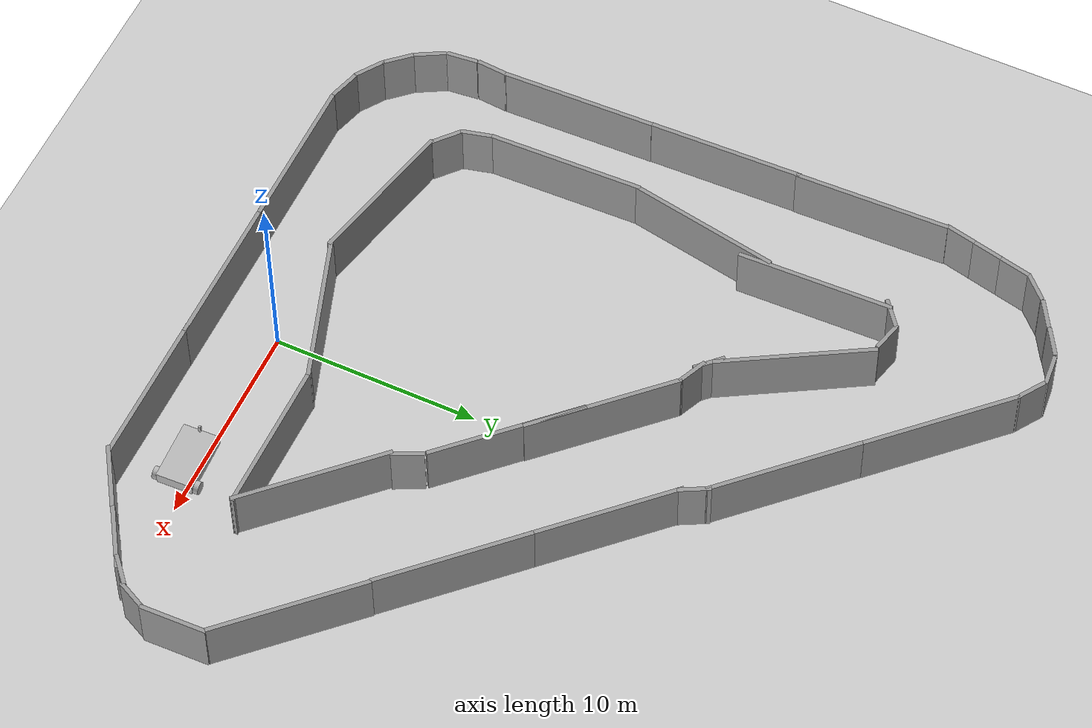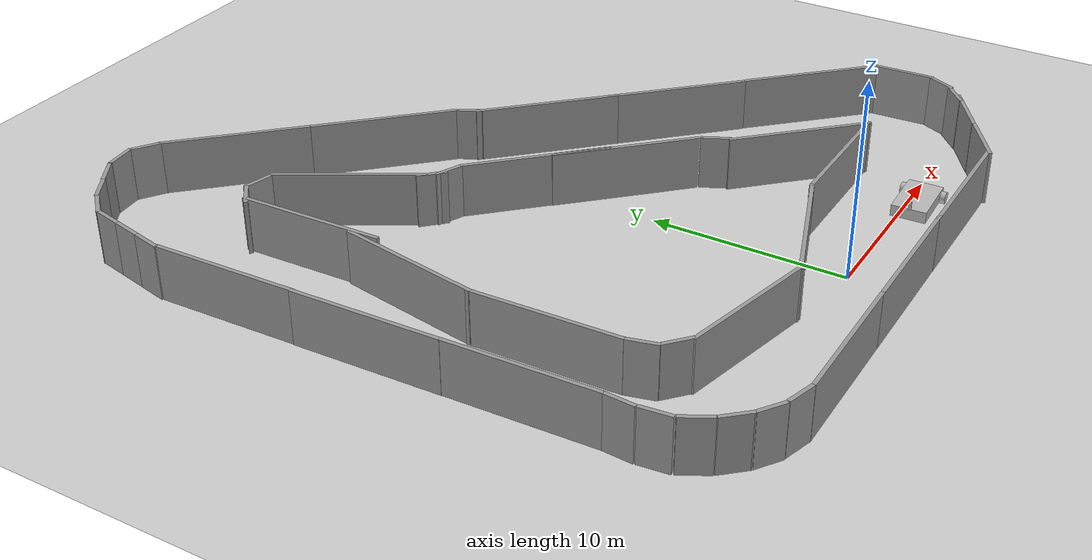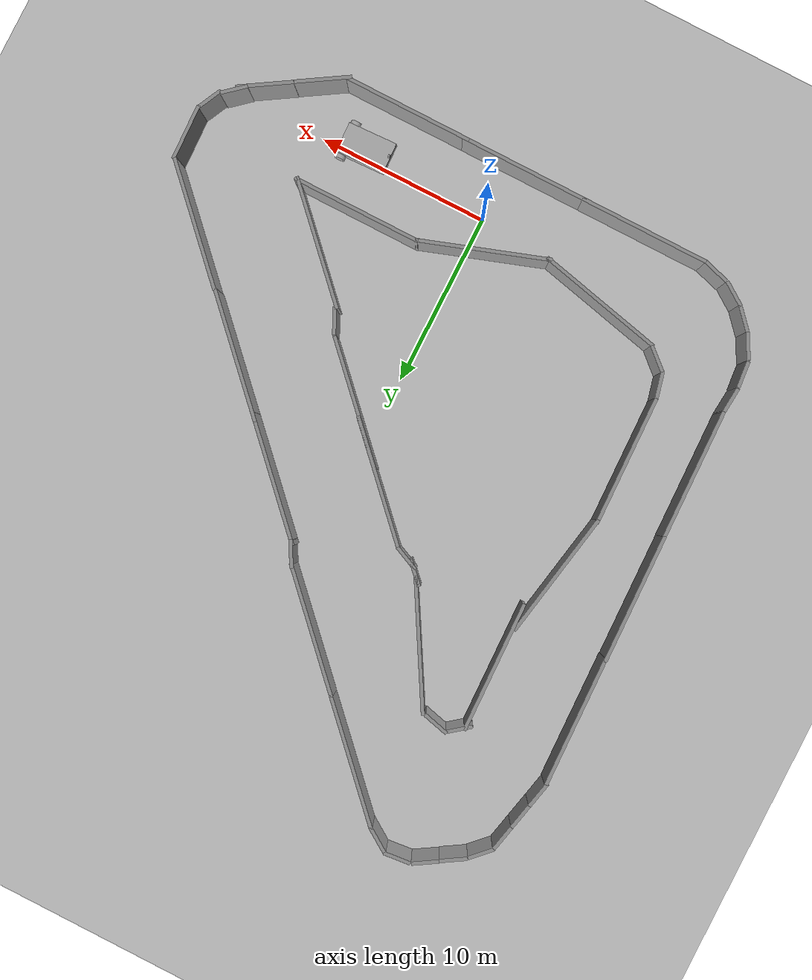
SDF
<sdf version="1.7">
 <world name="default">
  <light name="sun" type="directional">
   <pose>0 0 10 0 -0 0</pose>
   <diffuse>0.8 0.8 0.8 1</diffuse>
   <specular>0.2 0.2 0.2 1</specular>
   <attenuation>
    <range>1000</range>
    <constant>0.9</constant>
    <linear>0.01</linear>
    <quadratic>0.001</quadratic>
   </attenuation>
   <direction>-0.5 0.1 -0.9</direction>
   <spot><inner_angle>0</inner_angle><outer_angle>0</outer_angle><falloff>0</falloff></spot>
  </light>
  <model name="ground_plane">
   <static>1</static>
   <link name="link">
    <collision name="collision">
     <geometry><plane><normal>0 0 1</normal><size>100 100</size></plane></geometry>
     <surface>
      <contact><collide_bitmask>65535</collide_bitmask></contact>
      <friction><ode><mu>100</mu><mu2>50</mu2></ode></friction>
     </surface>
    </collision>
    <visual name="visual">
     <cast_shadows>0</cast_shadows>
     <geometry><plane><normal>0 0 1</normal><size>100 100</size></plane></geometry>
     <material>
      <script><uri>file://media/materials/scripts/gazebo.material</uri><name>Gazebo/Grey</name></script>
     </material>
    </visual>
   </link>
  </model>
  <gravity>0 0 -9.8</gravity>
  <magnetic_field>6e-06 2.3e-05 -4.2e-05</magnetic_field>
  <atmosphere type="adiabatic"/>
  <physics type="ode">
   <max_step_size>0.001</max_step_size>
   <real_time_factor>1</real_time_factor>
   <real_time_update_rate>1000</real_time_update_rate>
  </physics>
  <scene><ambient>0.4 0.4 0.4 1</ambient><background>0.7 0.7 0.7 1</background><shadows>1</shadows></scene>
  <spherical_coordinates>
   <surface_model>EARTH_WGS84</surface_model>
   <latitude_deg>0</latitude_deg>
   <longitude_deg>0</longitude_deg>
   <elevation>0</elevation>
   <heading_deg>0</heading_deg>
  </spherical_coordinates>
  <model name="grey_wall">
   <static>1</static>
   <link name="link">
    <pose>0 0 1.4 0 -0 0</pose>
    <collision name="collision"><geometry><box><size>7.5 0.2 2.8</size></box></geometry></collision>
    <visual name="visual">
     <cast_shadows>0</cast_shadows>
     <geometry><box><size>7.5 0.2 2.8</size></box></geometry>
     <material>
      <script>
       <uri>model://grey_wall/materials/scripts</uri>
       <uri>model://grey_wall/materials/textures</uri>
       <name>vrc/grey_wall</name>
      </script>
     </material>
    </visual>
   </link>
   <pose>6.24047 -3.07553 0 0 -0 0</pose>
  </model>
  <model name="grey_wall_0">
   <static>1</static>
   <link name="link">
    <pose>0 0 1.4 0 -0 0</pose>
    <collision name="collision"><geometry><box><size>7.5 0.2 2.8</size></box></geometry></collision>
    <visual name="visual">
     <cast_shadows>0</cast_shadows>
     <geometry><box><size>7.5 0.2 2.8</size></box></geometry>
     <material>
      <script>
       <uri>model://grey_wall/materials/scripts</uri>
       <uri>model://grey_wall/materials/textures</uri>
       <name>vrc/grey_wall</name>
      </script>
     </material>
    </visual>
   </link>
   <pose>6.195 3.06427 0 0 -0 0</pose>
  </model>
  <model name="grey_wall_1">
   <static>1</static>
   <link name="link">
    <pose>0 0 1.4 0 -0 0</pose>
    <collision name="collision"><geometry><box><size>7.5 0.2 2.8</size></box></geometry></collision>
    <visual name="visual">
     <cast_shadows>0</cast_shadows>
     <geometry><box><size>7.5 0.2 2.8</size></box></geometry>
     <material>
      <script>
       <uri>model://grey_wall/materials/scripts</uri>
       <uri>model://grey_wall/materials/textures</uri>
       <name>vrc/grey_wall</name>
      </script>
     </material>
    </visual>
   </link>
   <pose>-0.883506 -3.06915 0 0 -0 0</pose>
  </model>
  <model name="grey_wall_2">
   <static>1</static>
   <link name="link">
    <pose>0 0 1.4 0 -0 0</pose>
    <collision name="collision"><geometry><box><size>7.5 0.2 2.8</size></box></geometry></collision>
    <visual name="visual">
     <cast_shadows>0</cast_shadows>
     <geometry><box><size>7.5 0.2 2.8</size></box></geometry>
     <material>
      <script>
       <uri>model://grey_wall/materials/scripts</uri>
       <uri>model://grey_wall/materials/textures</uri>
       <name>vrc/grey_wall</name>
      </script>
     </material>
    </visual>
   </link>
   <pose>-0.930243 1.86057 0 0 -0 0.330047</pose>
  </model>
  <model name="grey_wall_3">
   <static>1</static>
   <link name="link">
    <pose>0 0 1.4 0 -0 0</pose>
    <collision name="collision"><geometry><box><size>7.5 0.2 2.8</size></box></geometry></collision>
    <visual name="visual">
     <cast_shadows>0</cast_shadows>
     <geometry><box><size>7.5 0.2 2.8</size></box></geometry>
     <material>
      <script>
       <uri>model://grey_wall/materials/scripts</uri>
       <uri>model://grey_wall/materials/textures</uri>
       <name>vrc/grey_wall</name>
      </script>
     </material>
    </visual>
   </link>
   <pose>-8.16793 -3.06567 0 0 -0 0</pose>
  </model>
  <model name="grey_wall_4">
   <static>1</static>
   <link name="link">
    <pose>0 0 1.4 0 -0 0</pose>
    <collision name="collision"><geometry><box><size>7.5 0.2 2.8</size></box></geometry></collision>
    <visual name="visual">
     <cast_shadows>0</cast_shadows>
     <geometry><box><size>7.5 0.2 2.8</size></box></geometry>
     <material>
      <script>
       <uri>model://grey_wall/materials/scripts</uri>
       <uri>model://grey_wall/materials/textures</uri>
       <name>vrc/grey_wall</name>
      </script>
     </material>
    </visual>
   </link>
   <pose>-7.83293 1.48595 0 0 0 -0.222426</pose>
  </model>
  <model name="grey_wall_small">
   <link name="link">
    <pose>0 0 1.4 0 -0 0</pose>
    <inertial>
     <inertia><ixx>0</ixx><ixy>0</ixy><ixz>0</ixz><iyy>0</iyy><iyz>0</iyz><izz>0</izz></inertia>
     <mass>0</mass>
    </inertial>
    <visual name="visual">
     <cast_shadows>0</cast_shadows>
     <geometry><box><size>1.53178 0.2 2.8</size></box></geometry>
     <material>
      <script>
       <uri>model://grey_wall/materials/scripts</uri>
       <uri>model://grey_wall/materials/textures</uri>
       <name>vrc/grey_wall</name>
      </script>
      <shader type="pixel"/>
     </material>
    </visual>
    <collision name="collision">
     <geometry><box><size>1.53178 0.2 2.8</size></box></geometry>
     <surface>
      <friction>
       <ode><mu>1</mu><mu2>1</mu2><fdir1>0 0 0</fdir1><slip1>0</slip1><slip2>0</slip2></ode>
       <torsional>
        <coefficient>1</coefficient>
        <patch_radius>0</patch_radius>
        <surface_radius>0</surface_radius>
        <use_patch_radius>1</use_patch_radius>
        <ode><slip>0</slip></ode>
       </torsional>
      </friction>
      <bounce><restitution_coefficient>0</restitution_coefficient><threshold>1e+06</threshold></bounce>
      <contact>
       <collide_without_contact>0</collide_without_contact>
       <collide_without_contact_bitmask>1</collide_without_contact_bitmask>
       <collide_bitmask>1</collide_bitmask>
       <ode>
        <soft_cfm>0</soft_cfm>
        <soft_erp>0.2</soft_erp>
        <kp>1e+13</kp>
        <kd>1</kd>
        <max_vel>0.01</max_vel>
        <min_depth>0</min_depth>
       </ode>
       <bullet>
        <split_impulse>1</split_impulse>
        <split_impulse_penetration_threshold>-0.01</split_impulse_penetration_threshold>
        <soft_cfm>0</soft_cfm>
        <soft_erp>0.2</soft_erp>
        <kp>1e+13</kp>
        <kd>1</kd>
       </bullet>
      </contact>
     </surface>
    </collision>
   </link>
   <static>1</static>
   <pose>-12.6395 -2.84604 -0 0 0 -0.284404</pose>
  </model>
  <model name="grey_wall_small_clone">
   <link name="link">
    <pose>0 0 1.4 0 -0 0</pose>
    <inertial>
     <inertia><ixx>0</ixx><ixy>0</ixy><ixz>0</ixz><iyy>0</iyy><iyz>0</iyz><izz>0</izz></inertia>
     <mass>0</mass>
    </inertial>
    <visual name="visual">
     <cast_shadows>0</cast_shadows>
     <geometry><box><size>1.53178 0.2 2.8</size></box></geometry>
     <material>
      <script>
       <uri>model://grey_wall/materials/scripts</uri>
       <uri>model://grey_wall/materials/textures</uri>
       <name>vrc/grey_wall</name>
      </script>
      <shader type="pixel"/>
     </material>
    </visual>
    <collision name="collision">
     <geometry><box><size>1.53178 0.2 2.8</size></box></geometry>
     <surface>
      <friction>
       <ode><mu>1</mu><mu2>1</mu2><fdir1>0 0 0</fdir1><slip1>0</slip1><slip2>0</slip2></ode>
       <torsional>
        <coefficient>1</coefficient>
        <patch_radius>0</patch_radius>
        <surface_radius>0</surface_radius>
        <use_patch_radius>1</use_patch_radius>
        <ode><slip>0</slip></ode>
       </torsional>
      </friction>
      <bounce><restitution_coefficient>0</restitution_coefficient><threshold>1e+06</threshold></bounce>
      <contact>
       <collide_without_contact>0</collide_without_contact>
       <collide_without_contact_bitmask>1</collide_without_contact_bitmask>
       <collide_bitmask>1</collide_bitmask>
       <ode>
        <soft_cfm>0</soft_cfm>
        <soft_erp>0.2</soft_erp>
        <kp>1e+13</kp>
        <kd>1</kd>
        <max_vel>0.01</max_vel>
        <min_depth>0</min_depth>
       </ode>
       <bullet>
        <split_impulse>1</split_impulse>
        <split_impulse_penetration_threshold>-0.01</split_impulse_penetration_threshold>
        <soft_cfm>0</soft_cfm>
        <soft_erp>0.2</soft_erp>
        <kp>1e+13</kp>
        <kd>1</kd>
       </bullet>
      </contact>
     </surface>
    </collision>
   </link>
   <static>1</static>
   <pose>-11.9422 2.81874 0 0 0 -0.719521</pose>
  </model>
  <model name="grey_wall_small_0">
   <link name="link">
    <pose>0 0 1.4 0 -0 0</pose>
    <inertial>
     <inertia><ixx>0</ixx><ixy>0</ixy><ixz>0</ixz><iyy>0</iyy><iyz>0</iyz><izz>0</izz></inertia>
     <mass>0</mass>
    </inertial>
    <visual name="visual">
     <cast_shadows>0</cast_shadows>
     <geometry><box><size>1.53178 0.2 2.8</size></box></geometry>
     <material>
      <script>
       <uri>model://grey_wall/materials/scripts</uri>
       <uri>model://grey_wall/materials/textures</uri>
       <name>vrc/grey_wall</name>
      </script>
      <shader type="pixel"/>
     </material>
    </visual>
    <collision name="collision">
     <geometry><box><size>1.53178 0.2 2.8</size></box></geometry>
     <surface>
      <friction>
       <ode><mu>1</mu><mu2>1</mu2><fdir1>0 0 0</fdir1><slip1>0</slip1><slip2>0</slip2></ode>
       <torsional>
        <coefficient>1</coefficient>
        <patch_radius>0</patch_radius>
        <surface_radius>0</surface_radius>
        <use_patch_radius>1</use_patch_radius>
        <ode><slip>0</slip></ode>
       </torsional>
      </friction>
      <bounce><restitution_coefficient>0</restitution_coefficient><threshold>1e+06</threshold></bounce>
      <contact>
       <collide_without_contact>0</collide_without_contact>
       <collide_without_contact_bitmask>1</collide_without_contact_bitmask>
       <collide_bitmask>1</collide_bitmask>
       <ode>
        <soft_cfm>0</soft_cfm>
        <soft_erp>0.2</soft_erp>
        <kp>1e+13</kp>
        <kd>1</kd>
        <max_vel>0.01</max_vel>
        <min_depth>0</min_depth>
       </ode>
       <bullet>
        <split_impulse>1</split_impulse>
        <split_impulse_penetration_threshold>-0.01</split_impulse_penetration_threshold>
        <soft_cfm>0</soft_cfm>
        <soft_erp>0.2</soft_erp>
        <kp>1e+13</kp>
        <kd>1</kd>
       </bullet>
      </contact>
     </surface>
    </collision>
   </link>
   <static>1</static>
   <pose>-14.0325 -2.21425 0 0 0 -0.600476</pose>
  </model>
  <model name="grey_wall_small_1">
   <link name="link">
    <pose>0 0 1.4 0 -0 0</pose>
    <inertial>
     <inertia><ixx>0</ixx><ixy>0</ixy><ixz>0</ixz><iyy>0</iyy><iyz>0</iyz><izz>0</izz></inertia>
     <mass>0</mass>
    </inertial>
    <visual name="visual">
     <cast_shadows>0</cast_shadows>
     <geometry><box><size>1.53178 0.2 2.8</size></box></geometry>
     <material>
      <script>
       <uri>model://grey_wall/materials/scripts</uri>
       <uri>model://grey_wall/materials/textures</uri>
       <name>vrc/grey_wall</name>
      </script>
      <shader type="pixel"/>
     </material>
    </visual>
    <collision name="collision">
     <geometry><box><size>1.53178 0.2 2.8</size></box></geometry>
     <surface>
      <friction>
       <ode><mu>1</mu><mu2>1</mu2><fdir1>0 0 0</fdir1><slip1>0</slip1><slip2>0</slip2></ode>
       <torsional>
        <coefficient>1</coefficient>
        <patch_radius>0</patch_radius>
        <surface_radius>0</surface_radius>
        <use_patch_radius>1</use_patch_radius>
        <ode><slip>0</slip></ode>
       </torsional>
      </friction>
      <bounce><restitution_coefficient>0</restitution_coefficient><threshold>1e+06</threshold></bounce>
      <contact>
       <collide_without_contact>0</collide_without_contact>
       <collide_without_contact_bitmask>1</collide_without_contact_bitmask>
       <collide_bitmask>1</collide_bitmask>
       <ode>
        <soft_cfm>0</soft_cfm>
        <soft_erp>0.2</soft_erp>
        <kp>1e+13</kp>
        <kd>1</kd>
        <max_vel>0.01</max_vel>
        <min_depth>0</min_depth>
       </ode>
       <bullet>
        <split_impulse>1</split_impulse>
        <split_impulse_penetration_threshold>-0.01</split_impulse_penetration_threshold>
        <soft_cfm>0</soft_cfm>
        <soft_erp>0.2</soft_erp>
        <kp>1e+13</kp>
        <kd>1</kd>
       </bullet>
      </contact>
     </surface>
    </collision>
   </link>
   <static>1</static>
   <pose>-15.1007 -1.27585 0 0 0 -0.833322</pose>
  </model>
  <model name="grey_wall_small_2">
   <link name="link">
    <pose>0 0 1.4 0 -0 0</pose>
    <inertial>
     <inertia><ixx>0</ixx><ixy>0</ixy><ixz>0</ixz><iyy>0</iyy><iyz>0</iyz><izz>0</izz></inertia>
     <mass>0</mass>
    </inertial>
    <visual name="visual">
     <cast_shadows>0</cast_shadows>
     <geometry><box><size>1.53178 0.2 2.8</size></box></geometry>
     <material>
      <script>
       <uri>model://grey_wall/materials/scripts</uri>
       <uri>model://grey_wall/materials/textures</uri>
       <name>vrc/grey_wall</name>
      </script>
      <shader type="pixel"/>
     </material>
    </visual>
    <collision name="collision">
     <geometry><box><size>1.53178 0.2 2.8</size></box></geometry>
     <surface>
      <friction>
       <ode><mu>1</mu><mu2>1</mu2><fdir1>0 0 0</fdir1><slip1>0</slip1><slip2>0</slip2></ode>
       <torsional>
        <coefficient>1</coefficient>
        <patch_radius>0</patch_radius>
        <surface_radius>0</surface_radius>
        <use_patch_radius>1</use_patch_radius>
        <ode><slip>0</slip></ode>
       </torsional>
      </friction>
      <bounce><restitution_coefficient>0</restitution_coefficient><threshold>1e+06</threshold></bounce>
      <contact>
       <collide_without_contact>0</collide_without_contact>
       <collide_without_contact_bitmask>1</collide_without_contact_bitmask>
       <collide_bitmask>1</collide_bitmask>
       <ode>
        <soft_cfm>0</soft_cfm>
        <soft_erp>0.2</soft_erp>
        <kp>1e+13</kp>
        <kd>1</kd>
        <max_vel>0.01</max_vel>
        <min_depth>0</min_depth>
       </ode>
       <bullet>
        <split_impulse>1</split_impulse>
        <split_impulse_penetration_threshold>-0.01</split_impulse_penetration_threshold>
        <soft_cfm>0</soft_cfm>
        <soft_erp>0.2</soft_erp>
        <kp>1e+13</kp>
        <kd>1</kd>
       </bullet>
      </contact>
     </surface>
    </collision>
   </link>
   <static>1</static>
   <pose>-15.9987 -0.025805 0 0 0 -1.06472</pose>
  </model>
  <model name="grey_wall_small_3">
   <link name="link">
    <pose>0 0 1.4 0 -0 0</pose>
    <inertial>
     <inertia><ixx>0</ixx><ixy>0</ixy><ixz>0</ixz><iyy>0</iyy><iyz>0</iyz><izz>0</izz></inertia>
     <mass>0</mass>
    </inertial>
    <visual name="visual">
     <cast_shadows>0</cast_shadows>
     <geometry><box><size>1.53178 0.2 2.8</size></box></geometry>
     <material>
      <script>
       <uri>model://grey_wall/materials/scripts</uri>
       <uri>model://grey_wall/materials/textures</uri>
       <name>vrc/grey_wall</name>
      </script>
      <shader type="pixel"/>
     </material>
    </visual>
    <collision name="collision">
     <geometry><box><size>1.53178 0.2 2.8</size></box></geometry>
     <surface>
      <friction>
       <ode><mu>1</mu><mu2>1</mu2><fdir1>0 0 0</fdir1><slip1>0</slip1><slip2>0</slip2></ode>
       <torsional>
        <coefficient>1</coefficient>
        <patch_radius>0</patch_radius>
        <surface_radius>0</surface_radius>
        <use_patch_radius>1</use_patch_radius>
        <ode><slip>0</slip></ode>
       </torsional>
      </friction>
      <bounce><restitution_coefficient>0</restitution_coefficient><threshold>1e+06</threshold></bounce>
      <contact>
       <collide_without_contact>0</collide_without_contact>
       <collide_without_contact_bitmask>1</collide_without_contact_bitmask>
       <collide_bitmask>1</collide_bitmask>
       <ode>
        <soft_cfm>0</soft_cfm>
        <soft_erp>0.2</soft_erp>
        <kp>1e+13</kp>
        <kd>1</kd>
        <max_vel>0.01</max_vel>
        <min_depth>0</min_depth>
       </ode>
       <bullet>
        <split_impulse>1</split_impulse>
        <split_impulse_penetration_threshold>-0.01</split_impulse_penetration_threshold>
        <soft_cfm>0</soft_cfm>
        <soft_erp>0.2</soft_erp>
        <kp>1e+13</kp>
        <kd>1</kd>
       </bullet>
      </contact>
     </surface>
    </collision>
   </link>
   <static>1</static>
   <pose>-16.4715 1.44928 -0 0 0 -1.4736</pose>
  </model>
  <model name="grey_wall_small_4">
   <link name="link">
    <pose>0 0 1.4 0 -0 0</pose>
    <inertial>
     <inertia><ixx>0</ixx><ixy>0</ixy><ixz>0</ixz><iyy>0</iyy><iyz>0</iyz><izz>0</izz></inertia>
     <mass>0</mass>
    </inertial>
    <visual name="visual">
     <cast_shadows>0</cast_shadows>
     <geometry><box><size>1.53178 0.2 2.8</size></box></geometry>
     <material>
      <script>
       <uri>model://grey_wall/materials/scripts</uri>
       <uri>model://grey_wall/materials/textures</uri>
       <name>vrc/grey_wall</name>
      </script>
      <shader type="pixel"/>
     </material>
    </visual>
    <collision name="collision">
     <geometry><box><size>1.53178 0.2 2.8</size></box></geometry>
     <surface>
      <friction>
       <ode><mu>1</mu><mu2>1</mu2><fdir1>0 0 0</fdir1><slip1>0</slip1><slip2>0</slip2></ode>
       <torsional>
        <coefficient>1</coefficient>
        <patch_radius>0</patch_radius>
        <surface_radius>0</surface_radius>
        <use_patch_radius>1</use_patch_radius>
        <ode><slip>0</slip></ode>
       </torsional>
      </friction>
      <bounce><restitution_coefficient>0</restitution_coefficient><threshold>1e+06</threshold></bounce>
      <contact>
       <collide_without_contact>0</collide_without_contact>
       <collide_without_contact_bitmask>1</collide_without_contact_bitmask>
       <collide_bitmask>1</collide_bitmask>
       <ode>
        <soft_cfm>0</soft_cfm>
        <soft_erp>0.2</soft_erp>
        <kp>1e+13</kp>
        <kd>1</kd>
        <max_vel>0.01</max_vel>
        <min_depth>0</min_depth>
       </ode>
       <bullet>
        <split_impulse>1</split_impulse>
        <split_impulse_penetration_threshold>-0.01</split_impulse_penetration_threshold>
        <soft_cfm>0</soft_cfm>
        <soft_erp>0.2</soft_erp>
        <kp>1e+13</kp>
        <kd>1</kd>
       </bullet>
      </contact>
     </surface>
    </collision>
   </link>
   <static>1</static>
   <pose>-12.7106 4.02154 0 0 0 -1.32722</pose>
  </model>
  <model name="grey_wall_small_5">
   <link name="link">
    <pose>0 0 1.4 0 -0 0</pose>
    <inertial>
     <inertia><ixx>0</ixx><ixy>0</ixy><ixz>0</ixz><iyy>0</iyy><iyz>0</iyz><izz>0</izz></inertia>
     <mass>0</mass>
    </inertial>
    <visual name="visual">
     <cast_shadows>0</cast_shadows>
     <geometry><box><size>1.53178 0.2 2.8</size></box></geometry>
     <material>
      <script>
       <uri>model://grey_wall/materials/scripts</uri>
       <uri>model://grey_wall/materials/textures</uri>
       <name>vrc/grey_wall</name>
      </script>
      <shader type="pixel"/>
     </material>
    </visual>
    <collision name="collision">
     <geometry><box><size>1.53178 0.2 2.8</size></box></geometry>
     <surface>
      <friction>
       <ode><mu>1</mu><mu2>1</mu2><fdir1>0 0 0</fdir1><slip1>0</slip1><slip2>0</slip2></ode>
       <torsional>
        <coefficient>1</coefficient>
        <patch_radius>0</patch_radius>
        <surface_radius>0</surface_radius>
        <use_patch_radius>1</use_patch_radius>
        <ode><slip>0</slip></ode>
       </torsional>
      </friction>
      <bounce><restitution_coefficient>0</restitution_coefficient><threshold>1e+06</threshold></bounce>
      <contact>
       <collide_without_contact>0</collide_without_contact>
       <collide_without_contact_bitmask>1</collide_without_contact_bitmask>
       <collide_bitmask>1</collide_bitmask>
       <ode>
        <soft_cfm>0</soft_cfm>
        <soft_erp>0.2</soft_erp>
        <kp>1e+13</kp>
        <kd>1</kd>
        <max_vel>0.01</max_vel>
        <min_depth>0</min_depth>
       </ode>
       <bullet>
        <split_impulse>1</split_impulse>
        <split_impulse_penetration_threshold>-0.01</split_impulse_penetration_threshold>
        <soft_cfm>0</soft_cfm>
        <soft_erp>0.2</soft_erp>
        <kp>1e+13</kp>
        <kd>1</kd>
       </bullet>
      </contact>
     </surface>
    </collision>
   </link>
   <static>1</static>
   <pose>-16.5119 3.01367 0 0 0 -1.64804</pose>
  </model>
  <model name="grey_wall_5">
   <static>1</static>
   <link name="link">
    <pose>0 0 1.4 0 -0 0</pose>
    <collision name="collision"><geometry><box><size>7.5 0.2 2.8</size></box></geometry></collision>
    <visual name="visual">
     <cast_shadows>0</cast_shadows>
     <geometry><box><size>7.5 0.2 2.8</size></box></geometry>
     <material>
      <script>
       <uri>model://grey_wall/materials/scripts</uri>
       <uri>model://grey_wall/materials/textures</uri>
       <name>vrc/grey_wall</name>
      </script>
     </material>
    </visual>
   </link>
   <pose>-16.5624 7.45087 0 0 0 -1.54263</pose>
  </model>
  <model name="grey_wall_5_clone">
   <static>1</static>
   <link name="link">
    <pose>0 0 1.4 0 -0 0</pose>
    <collision name="collision"><geometry><box><size>7.5 0.2 2.8</size></box></geometry></collision>
    <visual name="visual">
     <cast_shadows>0</cast_shadows>
     <geometry><box><size>7.5 0.2 2.8</size></box></geometry>
     <material>
      <script>
       <uri>model://grey_wall/materials/scripts</uri>
       <uri>model://grey_wall/materials/textures</uri>
       <name>vrc/grey_wall</name>
      </script>
     </material>
    </visual>
   </link>
   <pose>-13.0002 8.47563 0 0 0 -1.54263</pose>
  </model>
  <model name="grey_wall_5_clone_0">
   <static>1</static>
   <link name="link">
    <pose>0 0 1.4 0 -0 0</pose>
    <collision name="collision"><geometry><box><size>7.5 0.2 2.8</size></box></geometry></collision>
    <visual name="visual">
     <cast_shadows>0</cast_shadows>
     <geometry><box><size>7.5 0.2 2.8</size></box></geometry>
     <material>
      <script>
       <uri>model://grey_wall/materials/scripts</uri>
       <uri>model://grey_wall/materials/textures</uri>
       <name>vrc/grey_wall</name>
      </script>
     </material>
    </visual>
   </link>
   <pose>-16.7856 14.8865 0 0 0 -1.54263</pose>
  </model>
  <model name="grey_wall_5_clone_1">
   <static>1</static>
   <link name="link">
    <pose>0 0 1.4 0 -0 0</pose>
    <collision name="collision"><geometry><box><size>7.5 0.2 2.8</size></box></geometry></collision>
    <visual name="visual">
     <cast_shadows>0</cast_shadows>
     <geometry><box><size>7.5 0.2 2.8</size></box></geometry>
     <material>
      <script>
       <uri>model://grey_wall/materials/scripts</uri>
       <uri>model://grey_wall/materials/textures</uri>
       <name>vrc/grey_wall</name>
      </script>
     </material>
    </visual>
   </link>
   <pose>-12.4471 15.6811 0 0 0 -1.74901</pose>
  </model>
  <model name="grey_wall_5_clone_2">
   <static>1</static>
   <link name="link">
    <pose>0 0 1.4 0 -0 0</pose>
    <collision name="collision"><geometry><box><size>7.5 0.2 2.8</size></box></geometry></collision>
    <visual name="visual">
     <cast_shadows>0</cast_shadows>
     <geometry><box><size>7.5 0.2 2.8</size></box></geometry>
     <material>
      <script>
       <uri>model://grey_wall/materials/scripts</uri>
       <uri>model://grey_wall/materials/textures</uri>
       <name>vrc/grey_wall</name>
      </script>
     </material>
    </visual>
   </link>
   <pose>-16.9651 22.1924 0 0 0 -1.54263</pose>
  </model>
  <model name="grey_wall_5_clone_3">
   <static>1</static>
   <link name="link">
    <pose>0 0 1.4 0 -0 0</pose>
    <collision name="collision"><geometry><box><size>7.5 0.2 2.8</size></box></geometry></collision>
    <visual name="visual">
     <cast_shadows>0</cast_shadows>
     <geometry><box><size>7.5 0.2 2.8</size></box></geometry>
     <material>
      <script>
       <uri>model://grey_wall/materials/scripts</uri>
       <uri>model://grey_wall/materials/textures</uri>
       <name>vrc/grey_wall</name>
      </script>
     </material>
    </visual>
   </link>
   <pose>-11.7315 21.5967 0 0 0 -1.54263</pose>
  </model>
  <model name="grey_wall_small_6">
   <link name="link">
    <pose>0 0 1.4 0 -0 0</pose>
    <inertial>
     <inertia><ixx>0</ixx><ixy>0</ixy><ixz>0</ixz><iyy>0</iyy><iyz>0</iyz><izz>0</izz></inertia>
     <mass>0</mass>
    </inertial>
    <visual name="visual">
     <cast_shadows>0</cast_shadows>
     <geometry><box><size>1.53178 0.2 2.8</size></box></geometry>
     <material>
      <script>
       <uri>model://grey_wall/materials/scripts</uri>
       <uri>model://grey_wall/materials/textures</uri>
       <name>vrc/grey_wall</name>
      </script>
      <shader type="pixel"/>
     </material>
    </visual>
    <collision name="collision">
     <geometry><box><size>1.53178 0.2 2.8</size></box></geometry>
     <surface>
      <friction>
       <ode><mu>1</mu><mu2>1</mu2><fdir1>0 0 0</fdir1><slip1>0</slip1><slip2>0</slip2></ode>
       <torsional>
        <coefficient>1</coefficient>
        <patch_radius>0</patch_radius>
        <surface_radius>0</surface_radius>
        <use_patch_radius>1</use_patch_radius>
        <ode><slip>0</slip></ode>
       </torsional>
      </friction>
      <bounce><restitution_coefficient>0</restitution_coefficient><threshold>1e+06</threshold></bounce>
      <contact>
       <collide_without_contact>0</collide_without_contact>
       <collide_without_contact_bitmask>1</collide_without_contact_bitmask>
       <collide_bitmask>1</collide_bitmask>
       <ode>
        <soft_cfm>0</soft_cfm>
        <soft_erp>0.2</soft_erp>
        <kp>1e+13</kp>
        <kd>1</kd>
        <max_vel>0.01</max_vel>
        <min_depth>0</min_depth>
       </ode>
       <bullet>
        <split_impulse>1</split_impulse>
        <split_impulse_penetration_threshold>-0.01</split_impulse_penetration_threshold>
        <soft_cfm>0</soft_cfm>
        <soft_erp>0.2</soft_erp>
        <kp>1e+13</kp>
        <kd>1</kd>
       </bullet>
      </contact>
     </surface>
    </collision>
   </link>
   <static>1</static>
   <pose>-16.9602 26.6179 0 0 0 -1.78958</pose>
  </model>
  <model name="grey_wall_small_6_clone">
   <link name="link">
    <pose>0 0 1.4 0 -0 0</pose>
    <inertial>
     <inertia><ixx>0</ixx><ixy>0</ixy><ixz>0</ixz><iyy>0</iyy><iyz>0</iyz><izz>0</izz></inertia>
     <mass>0</mass>
    </inertial>
    <visual name="visual">
     <cast_shadows>0</cast_shadows>
     <geometry><box><size>1.53178 0.2 2.8</size></box></geometry>
     <material>
      <script>
       <uri>model://grey_wall/materials/scripts</uri>
       <uri>model://grey_wall/materials/textures</uri>
       <name>vrc/grey_wall</name>
      </script>
      <shader type="pixel"/>
     </material>
    </visual>
    <collision name="collision">
     <geometry><box><size>1.53178 0.2 2.8</size></box></geometry>
     <surface>
      <friction>
       <ode><mu>1</mu><mu2>1</mu2><fdir1>0 0 0</fdir1><slip1>0</slip1><slip2>0</slip2></ode>
       <torsional>
        <coefficient>1</coefficient>
        <patch_radius>0</patch_radius>
        <surface_radius>0</surface_radius>
        <use_patch_radius>1</use_patch_radius>
        <ode><slip>0</slip></ode>
       </torsional>
      </friction>
      <bounce><restitution_coefficient>0</restitution_coefficient><threshold>1e+06</threshold></bounce>
      <contact>
       <collide_without_contact>0</collide_without_contact>
       <collide_without_contact_bitmask>1</collide_without_contact_bitmask>
       <collide_bitmask>1</collide_bitmask>
       <ode>
        <soft_cfm>0</soft_cfm>
        <soft_erp>0.2</soft_erp>
        <kp>1e+13</kp>
        <kd>1</kd>
        <max_vel>0.01</max_vel>
        <min_depth>0</min_depth>
       </ode>
       <bullet>
        <split_impulse>1</split_impulse>
        <split_impulse_penetration_threshold>-0.01</split_impulse_penetration_threshold>
        <soft_cfm>0</soft_cfm>
        <soft_erp>0.2</soft_erp>
        <kp>1e+13</kp>
        <kd>1</kd>
       </bullet>
      </contact>
     </surface>
    </collision>
   </link>
   <static>1</static>
   <pose>-16.6343 28.0738 0 0 0 -1.78958</pose>
  </model>
  <model name="grey_wall_small_6_clone_0">
   <link name="link">
    <pose>0 0 1.4 0 -0 0</pose>
    <inertial>
     <inertia><ixx>0</ixx><ixy>0</ixy><ixz>0</ixz><iyy>0</iyy><iyz>0</iyz><izz>0</izz></inertia>
     <mass>0</mass>
    </inertial>
    <visual name="visual">
     <cast_shadows>0</cast_shadows>
     <geometry><box><size>1.53178 0.2 2.8</size></box></geometry>
     <material>
      <script>
       <uri>model://grey_wall/materials/scripts</uri>
       <uri>model://grey_wall/materials/textures</uri>
       <name>vrc/grey_wall</name>
      </script>
      <shader type="pixel"/>
     </material>
    </visual>
    <collision name="collision">
     <geometry><box><size>1.53178 0.2 2.8</size></box></geometry>
     <surface>
      <friction>
       <ode><mu>1</mu><mu2>1</mu2><fdir1>0 0 0</fdir1><slip1>0</slip1><slip2>0</slip2></ode>
       <torsional>
        <coefficient>1</coefficient>
        <patch_radius>0</patch_radius>
        <surface_radius>0</surface_radius>
        <use_patch_radius>1</use_patch_radius>
        <ode><slip>0</slip></ode>
       </torsional>
      </friction>
      <bounce><restitution_coefficient>0</restitution_coefficient><threshold>1e+06</threshold></bounce>
      <contact>
       <collide_without_contact>0</collide_without_contact>
       <collide_without_contact_bitmask>1</collide_without_contact_bitmask>
       <collide_bitmask>1</collide_bitmask>
       <ode>
        <soft_cfm>0</soft_cfm>
        <soft_erp>0.2</soft_erp>
        <kp>1e+13</kp>
        <kd>1</kd>
        <max_vel>0.01</max_vel>
        <min_depth>0</min_depth>
       </ode>
       <bullet>
        <split_impulse>1</split_impulse>
        <split_impulse_penetration_threshold>-0.01</split_impulse_penetration_threshold>
        <soft_cfm>0</soft_cfm>
        <soft_erp>0.2</soft_erp>
        <kp>1e+13</kp>
        <kd>1</kd>
       </bullet>
      </contact>
     </surface>
    </collision>
   </link>
   <static>1</static>
   <pose>-16.31 29.53 0 0 0 -1.78958</pose>
  </model>
  <model name="grey_wall_small_7">
   <link name="link">
    <pose>0 0 1.4 0 -0 0</pose>
    <inertial>
     <inertia><ixx>0</ixx><ixy>0</ixy><ixz>0</ixz><iyy>0</iyy><iyz>0</iyz><izz>0</izz></inertia>
     <mass>0</mass>
    </inertial>
    <visual name="visual">
     <cast_shadows>0</cast_shadows>
     <geometry><box><size>1.53178 0.2 2.8</size></box></geometry>
     <material>
      <script>
       <uri>model://grey_wall/materials/scripts</uri>
       <uri>model://grey_wall/materials/textures</uri>
       <name>vrc/grey_wall</name>
      </script>
      <shader type="pixel"/>
     </material>
    </visual>
    <collision name="collision">
     <geometry><box><size>1.53178 0.2 2.8</size></box></geometry>
     <surface>
      <friction>
       <ode><mu>1</mu><mu2>1</mu2><fdir1>0 0 0</fdir1><slip1>0</slip1><slip2>0</slip2></ode>
       <torsional>
        <coefficient>1</coefficient>
        <patch_radius>0</patch_radius>
        <surface_radius>0</surface_radius>
        <use_patch_radius>1</use_patch_radius>
        <ode><slip>0</slip></ode>
       </torsional>
      </friction>
      <bounce><restitution_coefficient>0</restitution_coefficient><threshold>1e+06</threshold></bounce>
      <contact>
       <collide_without_contact>0</collide_without_contact>
       <collide_without_contact_bitmask>1</collide_without_contact_bitmask>
       <collide_bitmask>1</collide_bitmask>
       <ode>
        <soft_cfm>0</soft_cfm>
        <soft_erp>0.2</soft_erp>
        <kp>1e+13</kp>
        <kd>1</kd>
        <max_vel>0.01</max_vel>
        <min_depth>0</min_depth>
       </ode>
       <bullet>
        <split_impulse>1</split_impulse>
        <split_impulse_penetration_threshold>-0.01</split_impulse_penetration_threshold>
        <soft_cfm>0</soft_cfm>
        <soft_erp>0.2</soft_erp>
        <kp>1e+13</kp>
        <kd>1</kd>
       </bullet>
      </contact>
     </surface>
    </collision>
   </link>
   <static>1</static>
   <pose>-15.667 30.7806 -0 0 -0 0.800233</pose>
  </model>
  <model name="grey_wall_small_8">
   <link name="link">
    <pose>0 0 1.4 0 -0 0</pose>
    <inertial>
     <inertia><ixx>0</ixx><ixy>0</ixy><ixz>0</ixz><iyy>0</iyy><iyz>0</iyz><izz>0</izz></inertia>
     <mass>0</mass>
    </inertial>
    <visual name="visual">
     <cast_shadows>0</cast_shadows>
     <geometry><box><size>1.53178 0.2 2.8</size></box></geometry>
     <material>
      <script>
       <uri>model://grey_wall/materials/scripts</uri>
       <uri>model://grey_wall/materials/textures</uri>
       <name>vrc/grey_wall</name>
      </script>
      <shader type="pixel"/>
     </material>
    </visual>
    <collision name="collision">
     <geometry><box><size>1.53178 0.2 2.8</size></box></geometry>
     <surface>
      <friction>
       <ode><mu>1</mu><mu2>1</mu2><fdir1>0 0 0</fdir1><slip1>0</slip1><slip2>0</slip2></ode>
       <torsional>
        <coefficient>1</coefficient>
        <patch_radius>0</patch_radius>
        <surface_radius>0</surface_radius>
        <use_patch_radius>1</use_patch_radius>
        <ode><slip>0</slip></ode>
       </torsional>
      </friction>
      <bounce><restitution_coefficient>0</restitution_coefficient><threshold>1e+06</threshold></bounce>
      <contact>
       <collide_without_contact>0</collide_without_contact>
       <collide_without_contact_bitmask>1</collide_without_contact_bitmask>
       <collide_bitmask>1</collide_bitmask>
       <ode>
        <soft_cfm>0</soft_cfm>
        <soft_erp>0.2</soft_erp>
        <kp>1e+13</kp>
        <kd>1</kd>
        <max_vel>0.01</max_vel>
        <min_depth>0</min_depth>
       </ode>
       <bullet>
        <split_impulse>1</split_impulse>
        <split_impulse_penetration_threshold>-0.01</split_impulse_penetration_threshold>
        <soft_cfm>0</soft_cfm>
        <soft_erp>0.2</soft_erp>
        <kp>1e+13</kp>
        <kd>1</kd>
       </bullet>
      </contact>
     </surface>
    </collision>
   </link>
   <static>1</static>
   <pose>-14.4817 31.7597 -0 0 -0 0.555531</pose>
  </model>
  <model name="grey_wall_small_8_clone">
   <link name="link">
    <pose>0 0 1.4 0 -0 0</pose>
    <inertial>
     <inertia><ixx>0</ixx><ixy>0</ixy><ixz>0</ixz><iyy>0</iyy><iyz>0</iyz><izz>0</izz></inertia>
     <mass>0</mass>
    </inertial>
    <visual name="visual">
     <cast_shadows>0</cast_shadows>
     <geometry><box><size>1.53178 0.2 2.8</size></box></geometry>
     <material>
      <script>
       <uri>model://grey_wall/materials/scripts</uri>
       <uri>model://grey_wall/materials/textures</uri>
       <name>vrc/grey_wall</name>
      </script>
      <shader type="pixel"/>
     </material>
    </visual>
    <collision name="collision">
     <geometry><box><size>1.53178 0.2 2.8</size></box></geometry>
     <surface>
      <friction>
       <ode><mu>1</mu><mu2>1</mu2><fdir1>0 0 0</fdir1><slip1>0</slip1><slip2>0</slip2></ode>
       <torsional>
        <coefficient>1</coefficient>
        <patch_radius>0</patch_radius>
        <surface_radius>0</surface_radius>
        <use_patch_radius>1</use_patch_radius>
        <ode><slip>0</slip></ode>
       </torsional>
      </friction>
      <bounce><restitution_coefficient>0</restitution_coefficient><threshold>1e+06</threshold></bounce>
      <contact>
       <collide_without_contact>0</collide_without_contact>
       <collide_without_contact_bitmask>1</collide_without_contact_bitmask>
       <collide_bitmask>1</collide_bitmask>
       <ode>
        <soft_cfm>0</soft_cfm>
        <soft_erp>0.2</soft_erp>
        <kp>1e+13</kp>
        <kd>1</kd>
        <max_vel>0.01</max_vel>
        <min_depth>0</min_depth>
       </ode>
       <bullet>
        <split_impulse>1</split_impulse>
        <split_impulse_penetration_threshold>-0.01</split_impulse_penetration_threshold>
        <soft_cfm>0</soft_cfm>
        <soft_erp>0.2</soft_erp>
        <kp>1e+13</kp>
        <kd>1</kd>
       </bullet>
      </contact>
     </surface>
    </collision>
   </link>
   <static>1</static>
   <pose>-13.2113 32.5753 -0 0 -0 0.555531</pose>
  </model>
  <model name="grey_wall_small_8_clone_0">
   <link name="link">
    <pose>0 0 1.4 0 -0 0</pose>
    <inertial>
     <inertia><ixx>0</ixx><ixy>0</ixy><ixz>0</ixz><iyy>0</iyy><iyz>0</iyz><izz>0</izz></inertia>
     <mass>0</mass>
    </inertial>
    <visual name="visual">
     <cast_shadows>0</cast_shadows>
     <geometry><box><size>1.53178 0.2 2.8</size></box></geometry>
     <material>
      <script>
       <uri>model://grey_wall/materials/scripts</uri>
       <uri>model://grey_wall/materials/textures</uri>
       <name>vrc/grey_wall</name>
      </script>
      <shader type="pixel"/>
     </material>
    </visual>
    <collision name="collision">
     <geometry><box><size>1.53178 0.2 2.8</size></box></geometry>
     <surface>
      <friction>
       <ode><mu>1</mu><mu2>1</mu2><fdir1>0 0 0</fdir1><slip1>0</slip1><slip2>0</slip2></ode>
       <torsional>
        <coefficient>1</coefficient>
        <patch_radius>0</patch_radius>
        <surface_radius>0</surface_radius>
        <use_patch_radius>1</use_patch_radius>
        <ode><slip>0</slip></ode>
       </torsional>
      </friction>
      <bounce><restitution_coefficient>0</restitution_coefficient><threshold>1e+06</threshold></bounce>
      <contact>
       <collide_without_contact>0</collide_without_contact>
       <collide_without_contact_bitmask>1</collide_without_contact_bitmask>
       <collide_bitmask>1</collide_bitmask>
       <ode>
        <soft_cfm>0</soft_cfm>
        <soft_erp>0.2</soft_erp>
        <kp>1e+13</kp>
        <kd>1</kd>
        <max_vel>0.01</max_vel>
        <min_depth>0</min_depth>
       </ode>
       <bullet>
        <split_impulse>1</split_impulse>
        <split_impulse_penetration_threshold>-0.01</split_impulse_penetration_threshold>
        <soft_cfm>0</soft_cfm>
        <soft_erp>0.2</soft_erp>
        <kp>1e+13</kp>
        <kd>1</kd>
       </bullet>
      </contact>
     </surface>
    </collision>
   </link>
   <static>1</static>
   <pose>-11.7464 33.068 0 0 -0 0.102813</pose>
  </model>
  <model name="grey_wall_6">
   <static>1</static>
   <link name="link">
    <pose>0 0 1.4 0 -0 0</pose>
    <collision name="collision"><geometry><box><size>7.5 0.2 2.8</size></box></geometry></collision>
    <visual name="visual">
     <cast_shadows>0</cast_shadows>
     <geometry><box><size>7.5 0.2 2.8</size></box></geometry>
     <material>
      <script>
       <uri>model://grey_wall/materials/scripts</uri>
       <uri>model://grey_wall/materials/textures</uri>
       <name>vrc/grey_wall</name>
      </script>
     </material>
    </visual>
   </link>
   <pose>7.26864 5.63896 -0 0 0 -0.79968</pose>
  </model>
  <model name="grey_wall_6_clone_1">
   <static>1</static>
   <link name="link">
    <pose>0 0 1.4 0 -0 0</pose>
    <collision name="collision"><geometry><box><size>7.5 0.2 2.8</size></box></geometry></collision>
    <visual name="visual">
     <cast_shadows>0</cast_shadows>
     <geometry><box><size>7.5 0.2 2.8</size></box></geometry>
     <material>
      <script>
       <uri>model://grey_wall/materials/scripts</uri>
       <uri>model://grey_wall/materials/textures</uri>
       <name>vrc/grey_wall</name>
      </script>
     </material>
    </visual>
   </link>
   <pose>-7.59676 22.4079 0 0 0 -1.04224</pose>
  </model>
  <model name="grey_wall_small_8_clone_clone">
   <link name="link">
    <pose>0 0 1.4 0 -0 0</pose>
    <inertial>
     <inertia><ixx>0</ixx><ixy>0</ixy><ixz>0</ixz><iyy>0</iyy><iyz>0</iyz><izz>0</izz></inertia>
     <mass>0</mass>
    </inertial>
    <visual name="visual">
     <cast_shadows>0</cast_shadows>
     <geometry><box><size>1.53178 0.2 2.8</size></box></geometry>
     <material>
      <script>
       <uri>model://grey_wall/materials/scripts</uri>
       <uri>model://grey_wall/materials/textures</uri>
       <name>vrc/grey_wall</name>
      </script>
      <shader type="pixel"/>
     </material>
    </visual>
    <collision name="collision">
     <geometry><box><size>1.53178 0.2 2.8</size></box></geometry>
     <surface>
      <friction>
       <ode><mu>1</mu><mu2>1</mu2><fdir1>0 0 0</fdir1><slip1>0</slip1><slip2>0</slip2></ode>
       <torsional>
        <coefficient>1</coefficient>
        <patch_radius>0</patch_radius>
        <surface_radius>0</surface_radius>
        <use_patch_radius>1</use_patch_radius>
        <ode><slip>0</slip></ode>
       </torsional>
      </friction>
      <bounce><restitution_coefficient>0</restitution_coefficient><threshold>1e+06</threshold></bounce>
      <contact>
       <collide_without_contact>0</collide_without_contact>
       <collide_without_contact_bitmask>1</collide_without_contact_bitmask>
       <collide_bitmask>1</collide_bitmask>
       <ode>
        <soft_cfm>0</soft_cfm>
        <soft_erp>0.2</soft_erp>
        <kp>1e+13</kp>
        <kd>1</kd>
        <max_vel>0.01</max_vel>
        <min_depth>0</min_depth>
       </ode>
       <bullet>
        <split_impulse>1</split_impulse>
        <split_impulse_penetration_threshold>-0.01</split_impulse_penetration_threshold>
        <soft_cfm>0</soft_cfm>
        <soft_erp>0.2</soft_erp>
        <kp>1e+13</kp>
        <kd>1</kd>
       </bullet>
      </contact>
     </surface>
    </collision>
   </link>
   <static>1</static>
   <pose>-10.3732 32.6921 0 0 0 -0.581724</pose>
  </model>
  <model name="grey_wall_6_clone_1_clone">
   <static>1</static>
   <link name="link">
    <pose>0 0 1.4 0 -0 0</pose>
    <collision name="collision"><geometry><box><size>7.5 0.2 2.8</size></box></geometry></collision>
    <visual name="visual">
     <cast_shadows>0</cast_shadows>
     <geometry><box><size>7.5 0.2 2.8</size></box></geometry>
     <material>
      <script>
       <uri>model://grey_wall/materials/scripts</uri>
       <uri>model://grey_wall/materials/textures</uri>
       <name>vrc/grey_wall</name>
      </script>
     </material>
    </visual>
   </link>
   <pose>-7.20728 29.6625 -0 0 0 -0.79968</pose>
  </model>
  <model name="grey_wall_6_clone_1_clone_0">
   <static>1</static>
   <link name="link">
    <pose>0 0 1.4 0 -0 0</pose>
    <collision name="collision"><geometry><box><size>7.5 0.2 2.8</size></box></geometry></collision>
    <visual name="visual">
     <cast_shadows>0</cast_shadows>
     <geometry><box><size>7.5 0.2 2.8</size></box></geometry>
     <material>
      <script>
       <uri>model://grey_wall/materials/scripts</uri>
       <uri>model://grey_wall/materials/textures</uri>
       <name>vrc/grey_wall</name>
      </script>
     </material>
    </visual>
   </link>
   <pose>-2.04813 24.3419 -0 0 0 -0.79968</pose>
  </model>
  <model name="grey_wall_small_10">
   <link name="link">
    <pose>0 0 1.4 0 -0 0</pose>
    <inertial>
     <inertia><ixx>0</ixx><ixy>0</ixy><ixz>0</ixz><iyy>0</iyy><iyz>0</iyz><izz>0</izz></inertia>
     <mass>0</mass>
    </inertial>
    <visual name="visual">
     <cast_shadows>0</cast_shadows>
     <geometry><box><size>1.53178 0.2 2.8</size></box></geometry>
     <material>
      <script>
       <uri>model://grey_wall/materials/scripts</uri>
       <uri>model://grey_wall/materials/textures</uri>
       <name>vrc/grey_wall</name>
      </script>
      <shader type="pixel"/>
     </material>
    </visual>
    <collision name="collision">
     <geometry><box><size>1.53178 0.2 2.8</size></box></geometry>
     <surface>
      <friction>
       <ode><mu>1</mu><mu2>1</mu2><fdir1>0 0 0</fdir1><slip1>0</slip1><slip2>0</slip2></ode>
       <torsional>
        <coefficient>1</coefficient>
        <patch_radius>0</patch_radius>
        <surface_radius>0</surface_radius>
        <use_patch_radius>1</use_patch_radius>
        <ode><slip>0</slip></ode>
       </torsional>
      </friction>
      <bounce><restitution_coefficient>0</restitution_coefficient><threshold>1e+06</threshold></bounce>
      <contact>
       <collide_without_contact>0</collide_without_contact>
       <collide_without_contact_bitmask>1</collide_without_contact_bitmask>
       <collide_bitmask>1</collide_bitmask>
       <ode>
        <soft_cfm>0</soft_cfm>
        <soft_erp>0.2</soft_erp>
        <kp>1e+13</kp>
        <kd>1</kd>
        <max_vel>0.01</max_vel>
        <min_depth>0</min_depth>
       </ode>
       <bullet>
        <split_impulse>1</split_impulse>
        <split_impulse_penetration_threshold>-0.01</split_impulse_penetration_threshold>
        <soft_cfm>0</soft_cfm>
        <soft_erp>0.2</soft_erp>
        <kp>1e+13</kp>
        <kd>1</kd>
       </bullet>
      </contact>
     </surface>
    </collision>
   </link>
   <static>1</static>
   <pose>-4.85073 18.5777 0 0 0 -0.421102</pose>
  </model>
  <model name="grey_wall_6_clone_1_clone_1">
   <static>1</static>
   <link name="link">
    <pose>0 0 1.4 0 -0 0</pose>
    <collision name="collision"><geometry><box><size>7.5 0.2 2.8</size></box></geometry></collision>
    <visual name="visual">
     <cast_shadows>0</cast_shadows>
     <geometry><box><size>7.5 0.2 2.8</size></box></geometry>
     <material>
      <script>
       <uri>model://grey_wall/materials/scripts</uri>
       <uri>model://grey_wall/materials/textures</uri>
       <name>vrc/grey_wall</name>
      </script>
     </material>
    </visual>
   </link>
   <pose>-1.62974 15.6407 -0 0 0 -0.79968</pose>
  </model>
  <model name="grey_wall_6_clone_1_clone_2">
   <static>1</static>
   <link name="link">
    <pose>0 0 1.4 0 -0 0</pose>
    <collision name="collision"><geometry><box><size>7.5 0.2 2.8</size></box></geometry></collision>
    <visual name="visual">
     <cast_shadows>0</cast_shadows>
     <geometry><box><size>7.5 0.2 2.8</size></box></geometry>
     <material>
      <script>
       <uri>model://grey_wall/materials/scripts</uri>
       <uri>model://grey_wall/materials/textures</uri>
       <name>vrc/grey_wall</name>
      </script>
     </material>
    </visual>
   </link>
   <pose>1.47741 12.391 -0 0 0 -0.79968</pose>
  </model>
  <model name="grey_wall_small_11">
   <link name="link">
    <pose>0 0 1.4 0 -0 0</pose>
    <inertial>
     <inertia><ixx>0</ixx><ixy>0</ixy><ixz>0</ixz><iyy>0</iyy><iyz>0</iyz><izz>0</izz></inertia>
     <mass>0</mass>
    </inertial>
    <visual name="visual">
     <cast_shadows>0</cast_shadows>
     <geometry><box><size>1.53178 0.2 2.8</size></box></geometry>
     <material>
      <script>
       <uri>model://grey_wall/materials/scripts</uri>
       <uri>model://grey_wall/materials/textures</uri>
       <name>vrc/grey_wall</name>
      </script>
      <shader type="pixel"/>
     </material>
    </visual>
    <collision name="collision">
     <geometry><box><size>1.53178 0.2 2.8</size></box></geometry>
     <surface>
      <friction>
       <ode><mu>1</mu><mu2>1</mu2><fdir1>0 0 0</fdir1><slip1>0</slip1><slip2>0</slip2></ode>
       <torsional>
        <coefficient>1</coefficient>
        <patch_radius>0</patch_radius>
        <surface_radius>0</surface_radius>
        <use_patch_radius>1</use_patch_radius>
        <ode><slip>0</slip></ode>
       </torsional>
      </friction>
      <bounce><restitution_coefficient>0</restitution_coefficient><threshold>1e+06</threshold></bounce>
      <contact>
       <collide_without_contact>0</collide_without_contact>
       <collide_without_contact_bitmask>1</collide_without_contact_bitmask>
       <collide_bitmask>1</collide_bitmask>
       <ode>
        <soft_cfm>0</soft_cfm>
        <soft_erp>0.2</soft_erp>
        <kp>1e+13</kp>
        <kd>1</kd>
        <max_vel>0.01</max_vel>
        <min_depth>0</min_depth>
       </ode>
       <bullet>
        <split_impulse>1</split_impulse>
        <split_impulse_penetration_threshold>-0.01</split_impulse_penetration_threshold>
        <soft_cfm>0</soft_cfm>
        <soft_erp>0.2</soft_erp>
        <kp>1e+13</kp>
        <kd>1</kd>
       </bullet>
      </contact>
     </surface>
    </collision>
   </link>
   <static>1</static>
   <pose>0.784588 21.1992 0 0 0 -1.08132</pose>
  </model>
  <model name="grey_wall_6_clone_1_clone_3">
   <static>1</static>
   <link name="link">
    <pose>0 0 1.4 0 -0 0</pose>
    <collision name="collision"><geometry><box><size>7.5 0.2 2.8</size></box></geometry></collision>
    <visual name="visual">
     <cast_shadows>0</cast_shadows>
     <geometry><box><size>7.5 0.2 2.8</size></box></geometry>
     <material>
      <script>
       <uri>model://grey_wall/materials/scripts</uri>
       <uri>model://grey_wall/materials/textures</uri>
       <name>vrc/grey_wall</name>
      </script>
     </material>
    </visual>
   </link>
   <pose>3.53604 18.0815 -0 0 0 -0.79968</pose>
  </model>
  <model name="grey_wall_small_12">
   <link name="link">
    <pose>0 0 1.4 0 -0 0</pose>
    <inertial>
     <inertia><ixx>0</ixx><ixy>0</ixy><ixz>0</ixz><iyy>0</iyy><iyz>0</iyz><izz>0</izz></inertia>
     <mass>0</mass>
    </inertial>
    <visual name="visual">
     <cast_shadows>0</cast_shadows>
     <geometry><box><size>1.53178 0.2 2.8</size></box></geometry>
     <material>
      <script>
       <uri>model://grey_wall/materials/scripts</uri>
       <uri>model://grey_wall/materials/textures</uri>
       <name>vrc/grey_wall</name>
      </script>
      <shader type="pixel"/>
     </material>
    </visual>
    <collision name="collision">
     <geometry><box><size>1.53178 0.2 2.8</size></box></geometry>
     <surface>
      <friction>
       <ode><mu>1</mu><mu2>1</mu2><fdir1>0 0 0</fdir1><slip1>0</slip1><slip2>0</slip2></ode>
       <torsional>
        <coefficient>1</coefficient>
        <patch_radius>0</patch_radius>
        <surface_radius>0</surface_radius>
        <use_patch_radius>1</use_patch_radius>
        <ode><slip>0</slip></ode>
       </torsional>
      </friction>
      <bounce><restitution_coefficient>0</restitution_coefficient><threshold>1e+06</threshold></bounce>
      <contact>
       <collide_without_contact>0</collide_without_contact>
       <collide_without_contact_bitmask>1</collide_without_contact_bitmask>
       <collide_bitmask>1</collide_bitmask>
       <ode>
        <soft_cfm>0</soft_cfm>
        <soft_erp>0.2</soft_erp>
        <kp>1e+13</kp>
        <kd>1</kd>
        <max_vel>0.01</max_vel>
        <min_depth>0</min_depth>
       </ode>
       <bullet>
        <split_impulse>1</split_impulse>
        <split_impulse_penetration_threshold>-0.01</split_impulse_penetration_threshold>
        <soft_cfm>0</soft_cfm>
        <soft_erp>0.2</soft_erp>
        <kp>1e+13</kp>
        <kd>1</kd>
       </bullet>
      </contact>
     </surface>
    </collision>
   </link>
   <static>1</static>
   <pose>4.48051 8.96075 -0 0 0 -1.12298</pose>
  </model>
  <model name="grey_wall_6_clone_1_clone_4">
   <static>1</static>
   <link name="link">
    <pose>0 0 1.4 0 -0 0</pose>
    <collision name="collision"><geometry><box><size>7.5 0.2 2.8</size></box></geometry></collision>
    <visual name="visual">
     <cast_shadows>0</cast_shadows>
     <geometry><box><size>7.5 0.2 2.8</size></box></geometry>
     <material>
      <script>
       <uri>model://grey_wall/materials/scripts</uri>
       <uri>model://grey_wall/materials/textures</uri>
       <name>vrc/grey_wall</name>
      </script>
     </material>
    </visual>
   </link>
   <pose>8.39752 13.0831 -0 0 0 -0.79968</pose>
  </model>
  <model name="grey_wall_6_clone_1_clone_5">
   <static>1</static>
   <link name="link">
    <pose>0 0 1.4 0 -0 0</pose>
    <collision name="collision"><geometry><box><size>7.5 0.2 2.8</size></box></geometry></collision>
    <visual name="visual">
     <cast_shadows>0</cast_shadows>
     <geometry><box><size>7.5 0.2 2.8</size></box></geometry>
     <material>
      <script>
       <uri>model://grey_wall/materials/scripts</uri>
       <uri>model://grey_wall/materials/textures</uri>
       <name>vrc/grey_wall</name>
      </script>
     </material>
    </visual>
   </link>
   <pose>13.62 7.76157 -0 0 0 -0.79968</pose>
  </model>
  <model name="grey_wall_medium">
   <link name="link">
    <pose>0 -0 1.4 -0 -0 -0</pose>
    <inertial>
     <inertia><ixx>0</ixx><ixy>0</ixy><ixz>0</ixz><iyy>0</iyy><iyz>0</iyz><izz>0</izz></inertia>
     <mass>0</mass>
    </inertial>
    <visual name="visual">
     <cast_shadows>0</cast_shadows>
     <geometry><box><size>3.18298 0.2 2.8</size></box></geometry>
     <material>
      <script>
       <uri>model://grey_wall/materials/scripts</uri>
       <uri>model://grey_wall/materials/textures</uri>
       <name>vrc/grey_wall</name>
      </script>
      <shader type="pixel"/>
     </material>
    </visual>
    <collision name="collision">
     <geometry><box><size>3.18298 0.2 2.8</size></box></geometry>
     <surface>
      <friction>
       <ode><mu>1</mu><mu2>1</mu2><fdir1>0 0 0</fdir1><slip1>0</slip1><slip2>0</slip2></ode>
       <torsional>
        <coefficient>1</coefficient>
        <patch_radius>0</patch_radius>
        <surface_radius>0</surface_radius>
        <use_patch_radius>1</use_patch_radius>
        <ode><slip>0</slip></ode>
       </torsional>
      </friction>
      <bounce><restitution_coefficient>0</restitution_coefficient><threshold>1e+06</threshold></bounce>
      <contact>
       <collide_without_contact>0</collide_without_contact>
       <collide_without_contact_bitmask>1</collide_without_contact_bitmask>
       <collide_bitmask>1</collide_bitmask>
       <ode>
        <soft_cfm>0</soft_cfm>
        <soft_erp>0.2</soft_erp>
        <kp>1e+13</kp>
        <kd>1</kd>
        <max_vel>0.01</max_vel>
        <min_depth>0</min_depth>
       </ode>
       <bullet>
        <split_impulse>1</split_impulse>
        <split_impulse_penetration_threshold>-0.01</split_impulse_penetration_threshold>
        <soft_cfm>0</soft_cfm>
        <soft_erp>0.2</soft_erp>
        <kp>1e+13</kp>
        <kd>1</kd>
       </bullet>
      </contact>
     </surface>
    </collision>
   </link>
   <static>1</static>
   <pose>16.3164 3.53392 -0 0 -0.007518 -1.53946</pose>
  </model>
  <model name="grey_wall_medium_clone">
   <link name="link">
    <pose>0 -0 1.4 -0 -0 -0</pose>
    <inertial>
     <inertia><ixx>0</ixx><ixy>0</ixy><ixz>0</ixz><iyy>0</iyy><iyz>0</iyz><izz>0</izz></inertia>
     <mass>0</mass>
    </inertial>
    <visual name="visual">
     <cast_shadows>0</cast_shadows>
     <geometry><box><size>3.18298 0.2 2.8</size></box></geometry>
     <material>
      <script>
       <uri>model://grey_wall/materials/scripts</uri>
       <uri>model://grey_wall/materials/textures</uri>
       <name>vrc/grey_wall</name>
      </script>
      <shader type="pixel"/>
     </material>
    </visual>
    <collision name="collision">
     <geometry><box><size>3.18298 0.2 2.8</size></box></geometry>
     <surface>
      <friction>
       <ode><mu>1</mu><mu2>1</mu2><fdir1>0 0 0</fdir1><slip1>0</slip1><slip2>0</slip2></ode>
       <torsional>
        <coefficient>1</coefficient>
        <patch_radius>0</patch_radius>
        <surface_radius>0</surface_radius>
        <use_patch_radius>1</use_patch_radius>
        <ode><slip>0</slip></ode>
       </torsional>
      </friction>
      <bounce><restitution_coefficient>0</restitution_coefficient><threshold>1e+06</threshold></bounce>
      <contact>
       <collide_without_contact>0</collide_without_contact>
       <collide_without_contact_bitmask>1</collide_without_contact_bitmask>
       <collide_bitmask>1</collide_bitmask>
       <ode>
        <soft_cfm>0</soft_cfm>
        <soft_erp>0.2</soft_erp>
        <kp>1e+13</kp>
        <kd>1</kd>
        <max_vel>0.01</max_vel>
        <min_depth>0</min_depth>
       </ode>
       <bullet>
        <split_impulse>1</split_impulse>
        <split_impulse_penetration_threshold>-0.01</split_impulse_penetration_threshold>
        <soft_cfm>0</soft_cfm>
        <soft_erp>0.2</soft_erp>
        <kp>1e+13</kp>
        <kd>1</kd>
       </bullet>
      </contact>
     </surface>
    </collision>
   </link>
   <static>1</static>
   <pose>11.067 -2.40478 -0 0.0065 -0.003778 -2.58367</pose>
  </model>
  <model name="grey_wall_medium_clone_clone">
   <link name="link">
    <pose>0 -0 1.4 -0 -0 -0</pose>
    <inertial>
     <inertia><ixx>0</ixx><ixy>0</ixy><ixz>0</ixz><iyy>0</iyy><iyz>0</iyz><izz>0</izz></inertia>
     <mass>0</mass>
    </inertial>
    <visual name="visual">
     <cast_shadows>0</cast_shadows>
     <geometry><box><size>3.18298 0.2 2.8</size></box></geometry>
     <material>
      <script>
       <uri>model://grey_wall/materials/scripts</uri>
       <uri>model://grey_wall/materials/textures</uri>
       <name>vrc/grey_wall</name>
      </script>
      <shader type="pixel"/>
     </material>
    </visual>
    <collision name="collision">
     <geometry><box><size>3.18298 0.2 2.8</size></box></geometry>
     <surface>
      <friction>
       <ode><mu>1</mu><mu2>1</mu2><fdir1>0 0 0</fdir1><slip1>0</slip1><slip2>0</slip2></ode>
       <torsional>
        <coefficient>1</coefficient>
        <patch_radius>0</patch_radius>
        <surface_radius>0</surface_radius>
        <use_patch_radius>1</use_patch_radius>
        <ode><slip>0</slip></ode>
       </torsional>
      </friction>
      <bounce><restitution_coefficient>0</restitution_coefficient><threshold>1e+06</threshold></bounce>
      <contact>
       <collide_without_contact>0</collide_without_contact>
       <collide_without_contact_bitmask>1</collide_without_contact_bitmask>
       <collide_bitmask>1</collide_bitmask>
       <ode>
        <soft_cfm>0</soft_cfm>
        <soft_erp>0.2</soft_erp>
        <kp>1e+13</kp>
        <kd>1</kd>
        <max_vel>0.01</max_vel>
        <min_depth>0</min_depth>
       </ode>
       <bullet>
        <split_impulse>1</split_impulse>
        <split_impulse_penetration_threshold>-0.01</split_impulse_penetration_threshold>
        <soft_cfm>0</soft_cfm>
        <soft_erp>0.2</soft_erp>
        <kp>1e+13</kp>
        <kd>1</kd>
       </bullet>
      </contact>
     </surface>
    </collision>
   </link>
   <static>1</static>
   <pose>13.7374 -0.716196 -0 0.0065 -0.003778 -2.58367</pose>
  </model>
  <model name="grey_wall_small_13">
   <link name="link">
    <pose>0 0 1.4 0 -0 0</pose>
    <inertial>
     <inertia><ixx>0</ixx><ixy>0</ixy><ixz>0</ixz><iyy>0</iyy><iyz>0</iyz><izz>0</izz></inertia>
     <mass>0</mass>
    </inertial>
    <visual name="visual">
     <cast_shadows>0</cast_shadows>
     <geometry><box><size>1.53178 0.2 2.8</size></box></geometry>
     <material>
      <script>
       <uri>model://grey_wall/materials/scripts</uri>
       <uri>model://grey_wall/materials/textures</uri>
       <name>vrc/grey_wall</name>
      </script>
      <shader type="pixel"/>
     </material>
    </visual>
    <collision name="collision">
     <geometry><box><size>1.53178 0.2 2.8</size></box></geometry>
     <surface>
      <friction>
       <ode><mu>1</mu><mu2>1</mu2><fdir1>0 0 0</fdir1><slip1>0</slip1><slip2>0</slip2></ode>
       <torsional>
        <coefficient>1</coefficient>
        <patch_radius>0</patch_radius>
        <surface_radius>0</surface_radius>
        <use_patch_radius>1</use_patch_radius>
        <ode><slip>0</slip></ode>
       </torsional>
      </friction>
      <bounce><restitution_coefficient>0</restitution_coefficient><threshold>1e+06</threshold></bounce>
      <contact>
       <collide_without_contact>0</collide_without_contact>
       <collide_without_contact_bitmask>1</collide_without_contact_bitmask>
       <collide_bitmask>1</collide_bitmask>
       <ode>
        <soft_cfm>0</soft_cfm>
        <soft_erp>0.2</soft_erp>
        <kp>1e+13</kp>
        <kd>1</kd>
        <max_vel>0.01</max_vel>
        <min_depth>0</min_depth>
       </ode>
       <bullet>
        <split_impulse>1</split_impulse>
        <split_impulse_penetration_threshold>-0.01</split_impulse_penetration_threshold>
        <soft_cfm>0</soft_cfm>
        <soft_erp>0.2</soft_erp>
        <kp>1e+13</kp>
        <kd>1</kd>
       </bullet>
      </contact>
     </surface>
    </collision>
   </link>
   <static>1</static>
   <pose>16.0165 1.37588 -0 0 -0 1.11487</pose>
  </model>
  <model name="grey_wall_small_14">
   <link name="link">
    <pose>0 0 1.4 0 -0 0</pose>
    <inertial>
     <inertia><ixx>0</ixx><ixy>0</ixy><ixz>0</ixz><iyy>0</iyy><iyz>0</iyz><izz>0</izz></inertia>
     <mass>0</mass>
    </inertial>
    <visual name="visual">
     <cast_shadows>0</cast_shadows>
     <geometry><box><size>1.53178 0.2 2.8</size></box></geometry>
     <material>
      <script>
       <uri>model://grey_wall/materials/scripts</uri>
       <uri>model://grey_wall/materials/textures</uri>
       <name>vrc/grey_wall</name>
      </script>
      <shader type="pixel"/>
     </material>
    </visual>
    <collision name="collision">
     <geometry><box><size>1.53178 0.2 2.8</size></box></geometry>
     <surface>
      <friction>
       <ode><mu>1</mu><mu2>1</mu2><fdir1>0 0 0</fdir1><slip1>0</slip1><slip2>0</slip2></ode>
       <torsional>
        <coefficient>1</coefficient>
        <patch_radius>0</patch_radius>
        <surface_radius>0</surface_radius>
        <use_patch_radius>1</use_patch_radius>
        <ode><slip>0</slip></ode>
       </torsional>
      </friction>
      <bounce><restitution_coefficient>0</restitution_coefficient><threshold>1e+06</threshold></bounce>
      <contact>
       <collide_without_contact>0</collide_without_contact>
       <collide_without_contact_bitmask>1</collide_without_contact_bitmask>
       <collide_bitmask>1</collide_bitmask>
       <ode>
        <soft_cfm>0</soft_cfm>
        <soft_erp>0.2</soft_erp>
        <kp>1e+13</kp>
        <kd>1</kd>
        <max_vel>0.01</max_vel>
        <min_depth>0</min_depth>
       </ode>
       <bullet>
        <split_impulse>1</split_impulse>
        <split_impulse_penetration_threshold>-0.01</split_impulse_penetration_threshold>
        <soft_cfm>0</soft_cfm>
        <soft_erp>0.2</soft_erp>
        <kp>1e+13</kp>
        <kd>1</kd>
       </bullet>
      </contact>
     </surface>
    </collision>
   </link>
   <static>1</static>
   <pose>15.0828 0.310917 0 0 -0 0.71303</pose>
  </model>
  <model name="grey_wall_small_9">
   <link name="link">
    <pose>0 0 1.4 0 -0 0</pose>
    <inertial>
     <inertia><ixx>0</ixx><ixy>0</ixy><ixz>0</ixz><iyy>0</iyy><iyz>0</iyz><izz>0</izz></inertia>
     <mass>0</mass>
    </inertial>
    <visual name="visual">
     <cast_shadows>0</cast_shadows>
     <geometry><box><size>1.53178 0.2 2.8</size></box></geometry>
     <material>
      <script>
       <uri>model://grey_wall/materials/scripts</uri>
       <uri>model://grey_wall/materials/textures</uri>
       <name>vrc/grey_wall</name>
      </script>
      <shader type="pixel"/>
     </material>
    </visual>
    <collision name="collision">
     <geometry><box><size>1.53178 0.2 2.8</size></box></geometry>
     <surface>
      <friction>
       <ode><mu>1</mu><mu2>1</mu2><fdir1>0 0 0</fdir1><slip1>0</slip1><slip2>0</slip2></ode>
       <torsional>
        <coefficient>1</coefficient>
        <patch_radius>0</patch_radius>
        <surface_radius>0</surface_radius>
        <use_patch_radius>1</use_patch_radius>
        <ode><slip>0</slip></ode>
       </torsional>
      </friction>
      <bounce><restitution_coefficient>0</restitution_coefficient><threshold>1e+06</threshold></bounce>
      <contact>
       <collide_without_contact>0</collide_without_contact>
       <collide_without_contact_bitmask>1</collide_without_contact_bitmask>
       <collide_bitmask>1</collide_bitmask>
       <ode>
        <soft_cfm>0</soft_cfm>
        <soft_erp>0.2</soft_erp>
        <kp>1e+13</kp>
        <kd>1</kd>
        <max_vel>0.01</max_vel>
        <min_depth>0</min_depth>
       </ode>
       <bullet>
        <split_impulse>1</split_impulse>
        <split_impulse_penetration_threshold>-0.01</split_impulse_penetration_threshold>
        <soft_cfm>0</soft_cfm>
        <soft_erp>0.2</soft_erp>
        <kp>1e+13</kp>
        <kd>1</kd>
       </bullet>
      </contact>
     </surface>
    </collision>
   </link>
   <static>1</static>
   <pose>-11.5518 25.4321 0 0 -0 0.671078</pose>
  </model>
  <model name="grey_wall_small_15">
   <link name="link">
    <pose>0 0 1.4 0 -0 0</pose>
    <inertial>
     <inertia><ixx>0</ixx><ixy>0</ixy><ixz>0</ixz><iyy>0</iyy><iyz>0</iyz><izz>0</izz></inertia>
     <mass>0</mass>
    </inertial>
    <visual name="visual">
     <cast_shadows>0</cast_shadows>
     <geometry><box><size>1.53178 0.2 2.8</size></box></geometry>
     <material>
      <script>
       <uri>model://grey_wall/materials/scripts</uri>
       <uri>model://grey_wall/materials/textures</uri>
       <name>vrc/grey_wall</name>
      </script>
      <shader type="pixel"/>
     </material>
    </visual>
    <collision name="collision">
     <geometry><box><size>1.53178 0.2 2.8</size></box></geometry>
     <surface>
      <friction>
       <ode><mu>1</mu><mu2>1</mu2><fdir1>0 0 0</fdir1><slip1>0</slip1><slip2>0</slip2></ode>
       <torsional>
        <coefficient>1</coefficient>
        <patch_radius>0</patch_radius>
        <surface_radius>0</surface_radius>
        <use_patch_radius>1</use_patch_radius>
        <ode><slip>0</slip></ode>
       </torsional>
      </friction>
      <bounce><restitution_coefficient>0</restitution_coefficient><threshold>1e+06</threshold></bounce>
      <contact>
       <collide_without_contact>0</collide_without_contact>
       <collide_without_contact_bitmask>1</collide_without_contact_bitmask>
       <collide_bitmask>1</collide_bitmask>
       <ode>
        <soft_cfm>0</soft_cfm>
        <soft_erp>0.2</soft_erp>
        <kp>1e+13</kp>
        <kd>1</kd>
        <max_vel>0.01</max_vel>
        <min_depth>0</min_depth>
       </ode>
       <bullet>
        <split_impulse>1</split_impulse>
        <split_impulse_penetration_threshold>-0.01</split_impulse_penetration_threshold>
        <soft_cfm>0</soft_cfm>
        <soft_erp>0.2</soft_erp>
        <kp>1e+13</kp>
        <kd>1</kd>
       </bullet>
      </contact>
     </surface>
    </collision>
   </link>
   <static>1</static>
   <pose>-10.3181 25.7474 0 0 0 -0.240845</pose>
  </model>
  <model name="grey_wall_small_16">
   <link name="link">
    <pose>0 0 1.4 0 -0 0</pose>
    <inertial>
     <inertia><ixx>0</ixx><ixy>0</ixy><ixz>0</ixz><iyy>0</iyy><iyz>0</iyz><izz>0</izz></inertia>
     <mass>0</mass>
    </inertial>
    <visual name="visual">
     <cast_shadows>0</cast_shadows>
     <geometry><box><size>1.53178 0.2 2.8</size></box></geometry>
     <material>
      <script>
       <uri>model://grey_wall/materials/scripts</uri>
       <uri>model://grey_wall/materials/textures</uri>
       <name>vrc/grey_wall</name>
      </script>
      <shader type="pixel"/>
     </material>
    </visual>
    <collision name="collision">
     <geometry><box><size>1.53178 0.2 2.8</size></box></geometry>
     <surface>
      <friction>
       <ode><mu>1</mu><mu2>1</mu2><fdir1>0 0 0</fdir1><slip1>0</slip1><slip2>0</slip2></ode>
       <torsional>
        <coefficient>1</coefficient>
        <patch_radius>0</patch_radius>
        <surface_radius>0</surface_radius>
        <use_patch_radius>1</use_patch_radius>
        <ode><slip>0</slip></ode>
       </torsional>
      </friction>
      <bounce><restitution_coefficient>0</restitution_coefficient><threshold>1e+06</threshold></bounce>
      <contact>
       <collide_without_contact>0</collide_without_contact>
       <collide_without_contact_bitmask>1</collide_without_contact_bitmask>
       <collide_bitmask>1</collide_bitmask>
       <ode>
        <soft_cfm>0</soft_cfm>
        <soft_erp>0.2</soft_erp>
        <kp>1e+13</kp>
        <kd>1</kd>
        <max_vel>0.01</max_vel>
        <min_depth>0</min_depth>
       </ode>
       <bullet>
        <split_impulse>1</split_impulse>
        <split_impulse_penetration_threshold>-0.01</split_impulse_penetration_threshold>
        <soft_cfm>0</soft_cfm>
        <soft_erp>0.2</soft_erp>
        <kp>1e+13</kp>
        <kd>1</kd>
       </bullet>
      </contact>
     </surface>
    </collision>
   </link>
   <static>1</static>
   <pose>-5.60065 19.0634 0 0 0 -0.785318</pose>
  </model>
  <model name="rugbot2">
   <link name="Root_link">
    <inertial>
     <pose>-0.250972 -1.6e-05 -0.049907 0 -0 0</pose>
     <mass>3.99272</mass>
     <inertia>
      <ixx>0.991134</ixx>
      <ixy>0</ixy>
      <ixz>0</ixz>
      <iyy>3.04884</iyy>
      <iyz>3.427e-05</iyz>
      <izz>3.70729</izz>
     </inertia>
    </inertial>
    <sensor name="laser1" type="ray">
     <visualize>1</visualize>
     <update_rate>10</update_rate>
     <ray>
      <scan>
       <horizontal>
        <samples>3</samples>
        <min_angle>1.5708</min_angle>
        <max_angle>-1.5708</max_angle>
        <resolution>1</resolution>
       </horizontal>
       <vertical><samples>1</samples><min_angle>0</min_angle><max_angle>0</max_angle></vertical>
      </scan>
      <range><min>0.3</min><max>12</max></range>
     </ray>
     <plugin name="gazebo_ros_head_hokuyo_controller" filename="libgazebo_ros_laser.so">
      <topicName>laser/scan</topicName>
      <frameName>laser</frameName>
      <robotNamespace>/</robotNamespace>
     </plugin>
     <pose>-1.32626 -0.04215 0.47358 0 -0 3.14</pose>
    </sensor>
    <visual name="Root_link_fixed_joint_lump__Diff_Bot__visual1_visual">
     <pose>-1 0 -0.2 0 -0 0</pose>
     <geometry><sphere><radius>0.2</radius></sphere></geometry>
     <material><shader type="pixel"><normal_map>__default__</normal_map></shader></material>
    </visual>
    <visual name="Root_link_fixed_joint_lump__rugbot.sdf__visual_visual_1">
     <pose>-1.32626 -0.04215 0.47358 0 -0 3.14</pose>
     <geometry><box><size>0.111563 0.119301 0.416724</size></box></geometry>
     <material><shader type="pixel"><normal_map>__default__</normal_map></shader></material>
    </visual>
    <visual name="Root_link_fixed_joint_lump__Diff_Bot__visual_visual_2">
     <pose>0.06283 -0.00211 0.02162 0 -0 0</pose>
     <geometry><box><size>2.88957 1.76304 0.587159</size></box></geometry>
     <material><shader type="pixel"><normal_map>__default__</normal_map></shader></material>
    </visual>
    <collision name="Root_link_fixed_joint_lump__Diff_Bot__collision_collision">
     <pose>-1 0 -0.2 0 -0 0</pose>
     <geometry><sphere><radius>0.2</radius></sphere></geometry>
     <surface>
      <friction>
       <ode><mu>3.46945e-18</mu><mu2>0</mu2><fdir1>0 0 0</fdir1><slip1>0</slip1><slip2>0</slip2></ode>
       <torsional>
        <coefficient>1</coefficient>
        <patch_radius>0</patch_radius>
        <surface_radius>0</surface_radius>
        <use_patch_radius>1</use_patch_radius>
        <ode><slip>0</slip></ode>
       </torsional>
      </friction>
      <bounce><restitution_coefficient>0</restitution_coefficient><threshold>1e+06</threshold></bounce>
      <contact>
       <collide_without_contact>0</collide_without_contact>
       <collide_without_contact_bitmask>1</collide_without_contact_bitmask>
       <collide_bitmask>1</collide_bitmask>
       <ode>
        <soft_cfm>0</soft_cfm>
        <soft_erp>0.2</soft_erp>
        <kp>1e+13</kp>
        <kd>1</kd>
        <max_vel>0.01</max_vel>
        <min_depth>0</min_depth>
       </ode>
       <bullet>
        <split_impulse>1</split_impulse>
        <split_impulse_penetration_threshold>-0.01</split_impulse_penetration_threshold>
        <soft_cfm>0</soft_cfm>
        <soft_erp>0.2</soft_erp>
        <kp>1e+13</kp>
        <kd>1</kd>
       </bullet>
      </contact>
     </surface>
    </collision>
    <collision name="Root_link_fixed_joint_lump__rugbot.sdf__collision_collision_1">
     <pose>-1.32626 -0.04215 0.47358 0 -0 3.14</pose>
     <geometry><box><size>0.111563 0.119301 0.416724</size></box></geometry>
     <surface>
      <friction>
       <ode><mu>1</mu><mu2>1</mu2><fdir1>0 0 0</fdir1><slip1>0</slip1><slip2>0</slip2></ode>
       <torsional>
        <coefficient>1</coefficient>
        <patch_radius>0</patch_radius>
        <surface_radius>0</surface_radius>
        <use_patch_radius>1</use_patch_radius>
        <ode><slip>0</slip></ode>
       </torsional>
      </friction>
      <bounce><restitution_coefficient>0</restitution_coefficient><threshold>1e+06</threshold></bounce>
      <contact>
       <collide_without_contact>0</collide_without_contact>
       <collide_without_contact_bitmask>1</collide_without_contact_bitmask>
       <collide_bitmask>1</collide_bitmask>
       <ode>
        <soft_cfm>0</soft_cfm>
        <soft_erp>0.2</soft_erp>
        <kp>1e+13</kp>
        <kd>1</kd>
        <max_vel>0.01</max_vel>
        <min_depth>0</min_depth>
       </ode>
       <bullet>
        <split_impulse>1</split_impulse>
        <split_impulse_penetration_threshold>-0.01</split_impulse_penetration_threshold>
        <soft_cfm>0</soft_cfm>
        <soft_erp>0.2</soft_erp>
        <kp>1e+13</kp>
        <kd>1</kd>
       </bullet>
      </contact>
     </surface>
    </collision>
    <collision name="Root_link_fixed_joint_lump__Diff_Bot__collision_collision_2">
     <pose>0.06283 -0.00211 0.02162 0 -0 0</pose>
     <geometry><box><size>2.88957 1.76304 0.587159</size></box></geometry>
     <surface>
      <friction>
       <ode><mu>1</mu><mu2>1</mu2><fdir1>0 0 0</fdir1><slip1>0</slip1><slip2>0</slip2></ode>
       <torsional>
        <coefficient>1</coefficient>
        <patch_radius>0</patch_radius>
        <surface_radius>0</surface_radius>
        <use_patch_radius>1</use_patch_radius>
        <ode><slip>0</slip></ode>
       </torsional>
      </friction>
      <bounce><restitution_coefficient>0</restitution_coefficient><threshold>1e+06</threshold></bounce>
      <contact>
       <collide_without_contact>0</collide_without_contact>
       <collide_without_contact_bitmask>1</collide_without_contact_bitmask>
       <collide_bitmask>1</collide_bitmask>
       <ode>
        <soft_cfm>0</soft_cfm>
        <soft_erp>0.2</soft_erp>
        <kp>1e+13</kp>
        <kd>1</kd>
        <max_vel>0.01</max_vel>
        <min_depth>0</min_depth>
       </ode>
       <bullet>
        <split_impulse>1</split_impulse>
        <split_impulse_penetration_threshold>-0.01</split_impulse_penetration_threshold>
        <soft_cfm>0</soft_cfm>
        <soft_erp>0.2</soft_erp>
        <kp>1e+13</kp>
        <kd>1</kd>
       </bullet>
      </contact>
     </surface>
    </collision>
   </link>
   <link name="Diff_Bot__link_1">
    <pose>1.20761 1.01943 -0.07838 1.5707 -0 0</pose>
    <inertial>
     <mass>1</mass>
     <inertia><ixx>0.145833</ixx><ixy>0</ixy><ixz>0</ixz><iyy>0.145833</iyy><iyz>0</iyz><izz>0.125</izz></inertia>
    </inertial>
    <visual name="Diff_Bot__link_1_fixed_joint_lump__Diff_Bot__visual_visual">
     <geometry><cylinder><length>0.25</length><radius>0.3</radius></cylinder></geometry>
     <material><shader type="pixel"><normal_map>__default__</normal_map></shader></material>
    </visual>
    <collision name="Diff_Bot__link_1_fixed_joint_lump__Diff_Bot__collision_collision">
     <geometry><cylinder><radius>0.3</radius><length>0.25</length></cylinder></geometry>
     <surface>
      <friction>
       <ode><mu>100</mu><mu2>100</mu2><fdir1>0 0 0</fdir1><slip1>0</slip1><slip2>0</slip2></ode>
       <torsional>
        <coefficient>1</coefficient>
        <patch_radius>0</patch_radius>
        <surface_radius>0</surface_radius>
        <use_patch_radius>1</use_patch_radius>
        <ode><slip>0</slip></ode>
       </torsional>
      </friction>
      <bounce><restitution_coefficient>0</restitution_coefficient><threshold>1e+06</threshold></bounce>
      <contact>
       <collide_without_contact>0</collide_without_contact>
       <collide_without_contact_bitmask>1</collide_without_contact_bitmask>
       <collide_bitmask>1</collide_bitmask>
       <ode>
        <soft_cfm>0</soft_cfm>
        <soft_erp>0.2</soft_erp>
        <kp>1e+13</kp>
        <kd>1</kd>
        <max_vel>0.01</max_vel>
        <min_depth>0</min_depth>
       </ode>
       <bullet>
        <split_impulse>1</split_impulse>
        <split_impulse_penetration_threshold>-0.01</split_impulse_penetration_threshold>
        <soft_cfm>0</soft_cfm>
        <soft_erp>0.2</soft_erp>
        <kp>1e+13</kp>
        <kd>1</kd>
       </bullet>
      </contact>
     </surface>
    </collision>
   </link>
   <link name="Diff_Bot__link_1_clone">
    <pose>1.20761 -1.00867 -0.07838 1.5707 -0 0</pose>
    <inertial>
     <mass>1</mass>
     <inertia><ixx>0.145833</ixx><ixy>0</ixy><ixz>0</ixz><iyy>0.145833</iyy><iyz>0</iyz><izz>0.125</izz></inertia>
    </inertial>
    <visual name="Diff_Bot__link_1_clone_fixed_joint_lump__Diff_Bot__visual_visual">
     <geometry><cylinder><length>0.25</length><radius>0.3</radius></cylinder></geometry>
     <material><shader type="pixel"><normal_map>__default__</normal_map></shader></material>
    </visual>
    <collision name="Diff_Bot__link_1_clone_fixed_joint_lump__Diff_Bot__collision_collision">
     <geometry><cylinder><radius>0.3</radius><length>0.25</length></cylinder></geometry>
     <surface>
      <friction>
       <ode><mu>100</mu><mu2>100</mu2><fdir1>0 0 0</fdir1><slip1>0</slip1><slip2>0</slip2></ode>
       <torsional>
        <coefficient>1</coefficient>
        <patch_radius>0</patch_radius>
        <surface_radius>0</surface_radius>
        <use_patch_radius>1</use_patch_radius>
        <ode><slip>0</slip></ode>
       </torsional>
      </friction>
      <bounce><restitution_coefficient>0</restitution_coefficient><threshold>1e+06</threshold></bounce>
      <contact>
       <collide_without_contact>0</collide_without_contact>
       <collide_without_contact_bitmask>1</collide_without_contact_bitmask>
       <collide_bitmask>1</collide_bitmask>
       <ode>
        <soft_cfm>0</soft_cfm>
        <soft_erp>0.2</soft_erp>
        <kp>1e+13</kp>
        <kd>1</kd>
        <max_vel>0.01</max_vel>
        <min_depth>0</min_depth>
       </ode>
       <bullet>
        <split_impulse>1</split_impulse>
        <split_impulse_penetration_threshold>-0.01</split_impulse_penetration_threshold>
        <soft_cfm>0</soft_cfm>
        <soft_erp>0.2</soft_erp>
        <kp>1e+13</kp>
        <kd>1</kd>
       </bullet>
      </contact>
     </surface>
    </collision>
   </link>
   <joint name="Diff_Bot__link_0_JOINT_1" type="revolute">
    <parent>Root_link</parent>
    <child>Diff_Bot__link_1</child>
    <axis>
     <xyz>0 0 1</xyz>
     <limit><lower>-1e+16</lower><upper>1e+16</upper><effort>-1</effort><velocity>-1</velocity></limit>
     <dynamics>
      <spring_reference>0</spring_reference>
      <spring_stiffness>0</spring_stiffness>
      <damping>0</damping>
      <friction>0</friction>
     </dynamics>
    </axis>
    <physics>
     <ode><limit><cfm>0</cfm><erp>0.2</erp></limit><suspension><cfm>0</cfm><erp>0.2</erp></suspension></ode>
    </physics>
   </joint>
   <joint name="Diff_Bot__link_0_JOINT_2" type="revolute">
    <parent>Root_link</parent>
    <child>Diff_Bot__link_1_clone</child>
    <axis>
     <xyz>0 0 1</xyz>
     <limit><lower>-1e+16</lower><upper>1e+16</upper><effort>-1</effort><velocity>-1</velocity></limit>
     <dynamics>
      <spring_reference>0</spring_reference>
      <spring_stiffness>0</spring_stiffness>
      <damping>0</damping>
      <friction>0</friction>
     </dynamics>
    </axis>
    <physics>
     <ode><limit><cfm>0</cfm><erp>0.2</erp></limit><suspension><cfm>0</cfm><erp>0.2</erp></suspension></ode>
    </physics>
   </joint>
   <static>0</static>
   <plugin name="differential_drive_controller" filename="libgazebo_ros_diff_drive.so">
    <updateRate>100</updateRate>
    <leftJoint>Diff_Bot__link_0_JOINT_2</leftJoint>
    <rightJoint>Diff_Bot__link_0_JOINT_1</rightJoint>
    <wheelSeparation>2.01304</wheelSeparation>
    <wheelDiameter>0.6</wheelDiameter>
    <wheelAcceleration>0</wheelAcceleration>
    <wheelTorque>20</wheelTorque>
    <commandTopic>cmd_vel</commandTopic>
    <odometryTopic>odom</odometryTopic>
    <odometryFrame>odom</odometryFrame>
    <robotBaseFrame>base_footprint</robotBaseFrame>
    <odometrySource>1</odometrySource>
    <publishWheelTF>1</publishWheelTF>
    <publishOdom>1</publishOdom>
    <publishWheelJointState>1</publishWheelJointState>
    <legacyMode>0</legacyMode>
    <robotNamespace>/</robotNamespace>
   </plugin>
   <pose>7.51676 -0.560226 0.390205 0.00113 0.00972 0.041134</pose>
  </model>
 </world>
</sdf>
